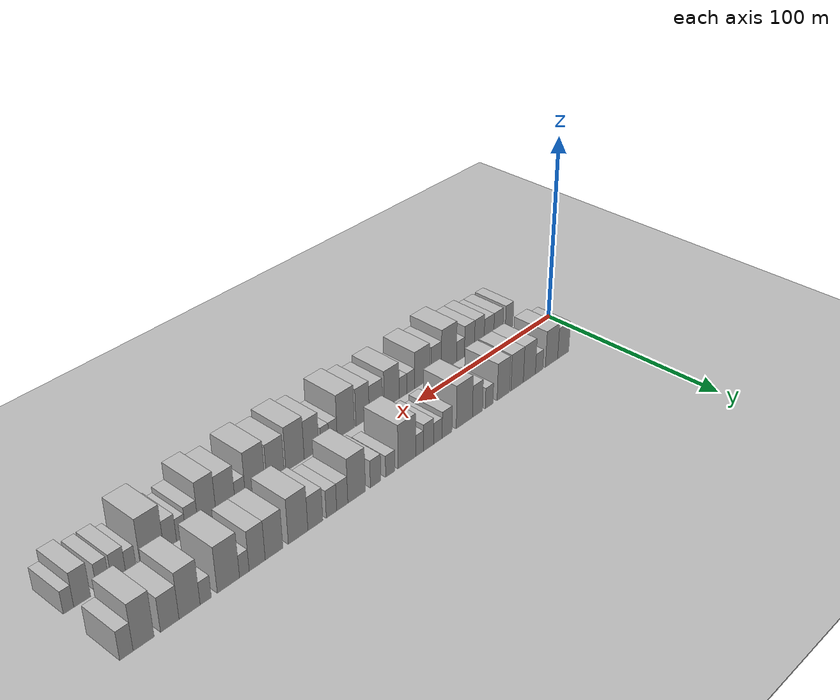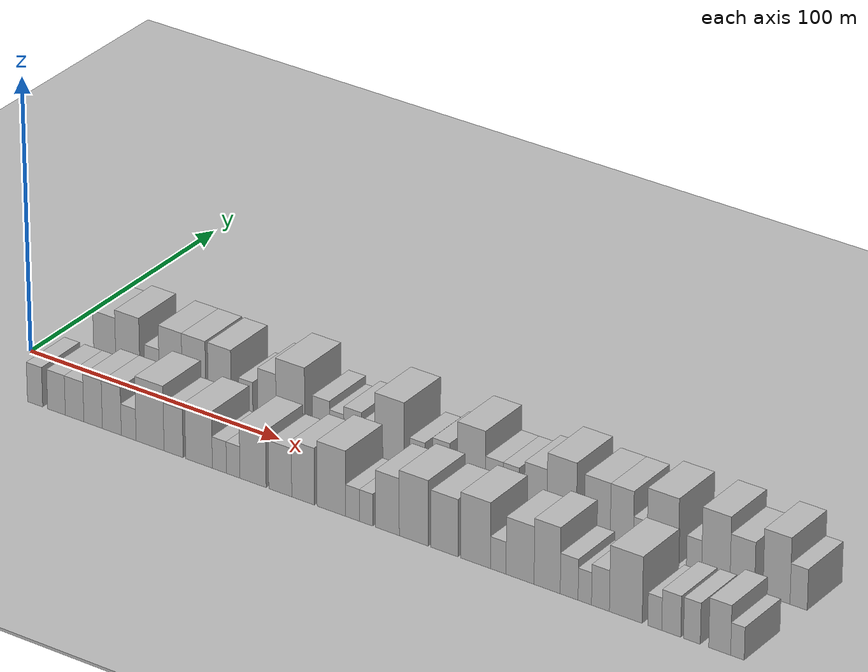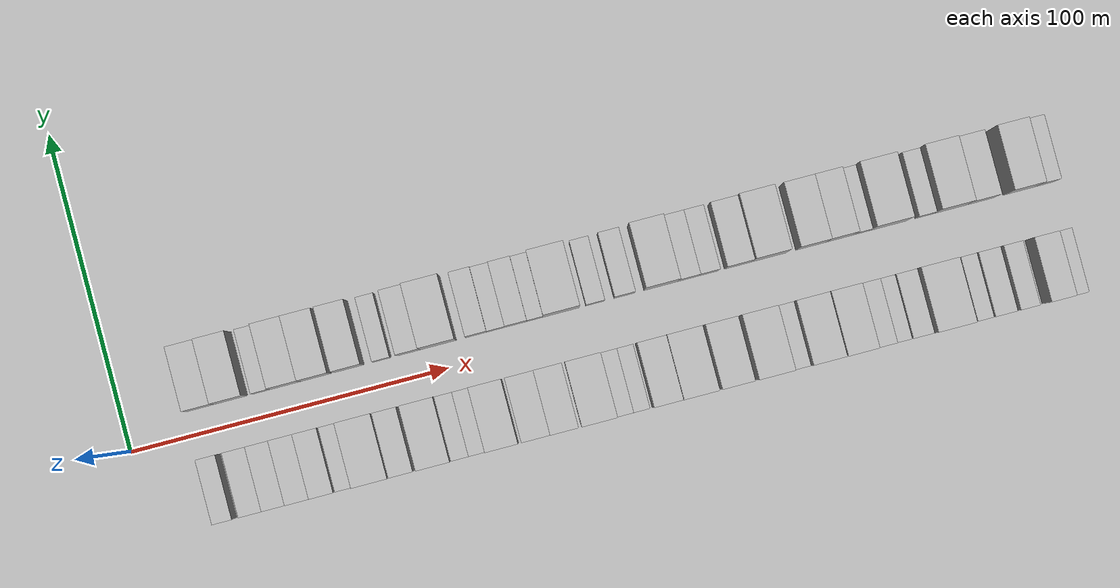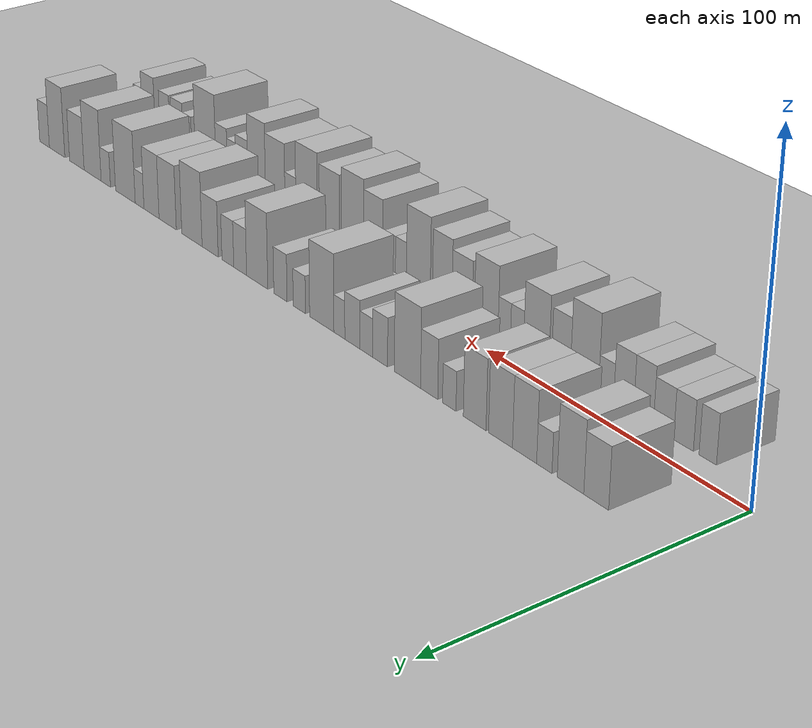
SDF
<?xml version="1.0" encoding="utf-8"?>

<sdf version="1.6">

   <world name="default">

      <gui fullscreen="0">

         <camera name="user_camera">

            <pose>-15 0 4.57585 0 0 0</pose>

            <view_controller>orbit</view_controller>

         </camera>

      </gui>

      <scene>

         <sky>

           <clouds>

             <speed>12</speed>

           </clouds>

         </sky>

         <ambient>0.4 0.4 0.4 1</ambient>

         <background>0.7 0.7 0.7 1</background>

         <shadows>1</shadows>

      </scene>

      <gravity>0 0 -9.8066</gravity>

      <magnetic_field>6e-06 2.3e-05 -4.2e-05</magnetic_field>

      <physics default="0" name="default_physics" type="ode">

         <ode>

            <solver>

               <type>quick</type>

               <iters>10</iters>

               <sor>1.0</sor>

               <use_dynamic_moi_rescaling>0</use_dynamic_moi_rescaling>

            </solver>

            <constraints>

               <cfm>0</cfm>

               <erp>0.2</erp>

               <contact_max_correcting_vel>100</contact_max_correcting_vel>

               <contact_surface_layer>0.001</contact_surface_layer>

            </constraints>

         </ode>

         <max_step_size>0.004</max_step_size>

         <real_time_factor>1</real_time_factor>

         <real_time_update_rate>250</real_time_update_rate>

      </physics>

      <light name="sun" type="directional">

         <cast_shadows>1</cast_shadows>

         <pose>0 0 10 0 0 0</pose>

         <diffuse>0.8 0.8 0.8 1</diffuse>

         <specular>0.2 0.2 0.2 1</specular>

         <attenuation>

            <range>1000</range>

            <constant>0.9</constant>

            <linear>0.01</linear>

            <quadratic>0.001</quadratic>

         </attenuation>

         <direction>-0.5 0.1 -0.9</direction>

      </light>

      <include>

         <name>ground_plane_1</name>

         <uri>model://HANNAS_ground_plane</uri>

         <pose>0 0 0  0 0 0</pose>

      </include>

      <include>

         <name>ground_plane_2</name>

         <uri>model://HANNAS_ground_plane</uri>

         <pose>100 0 0  0 0 0</pose>

      </include>

      <model name="building_1">

         <static>1</static>

         <pose frame="">24.4732 17.5000 0 0.000000 0.000000 1.570796</pose>

         <link name="link">

            <pose frame="">0 0 9.00 0 0 0</pose>

            <collision name="collision">

               <geometry>

                  <box>

                     <size>20.0000 8.9463 18.0000</size>

                  </box>

               </geometry>

               <max_contacts>10</max_contacts>

               <surface>

                  <contact>

                     <ode/>

                  </contact>

                  <bounce/>

                  <friction>

                     <torsional>

                        <ode/>

                     </torsional>

                     <ode/>

                  </friction>

               </surface>

            </collision>

            <visual name="visual">

               <cast_shadows>0</cast_shadows>

               <geometry>

                  <box>

                     <size>20.0000 8.9463 18.0000</size>

                  </box>

               </geometry>

               <material>

                  <script>

                     <uri>model://HANNAS_wall/materials/scripts</uri>

                     <uri>model://HANNAS_wall/materials/textures</uri>

                     <name>vrc/HANNAS_wall</name>

                  </script>

               </material>

            </visual>

            <self_collide>0</self_collide>

            <enable_wind>0</enable_wind>

            <kinematic>0</kinematic>

         </link>

      </model>

      <model name="building_2">

         <static>1</static>

         <pose frame="">33.8260 17.5000 0 0.000000 0.000000 1.570796</pose>

         <link name="link">

            <pose frame="">0 0 10.50 0 0 0</pose>

            <collision name="collision">

               <geometry>

                  <box>

                     <size>20.0000 9.7593 21.0000</size>

                  </box>

               </geometry>

               <max_contacts>10</max_contacts>

               <surface>

                  <contact>

                     <ode/>

                  </contact>

                  <bounce/>

                  <friction>

                     <torsional>

                        <ode/>

                     </torsional>

                     <ode/>

                  </friction>

               </surface>

            </collision>

            <visual name="visual">

               <cast_shadows>0</cast_shadows>

               <geometry>

                  <box>

                     <size>20.0000 9.7593 21.0000</size>

                  </box>

               </geometry>

               <material>

                  <script>

                     <uri>model://HANNAS_wall/materials/scripts</uri>

                     <uri>model://HANNAS_wall/materials/textures</uri>

                     <name>vrc/HANNAS_wall</name>

                  </script>

               </material>

            </visual>

            <self_collide>0</self_collide>

            <enable_wind>0</enable_wind>

            <kinematic>0</kinematic>

         </link>

      </model>

      <model name="building_3">

         <static>1</static>

         <pose frame="">43.6046 17.5000 0 0.000000 0.000000 1.570796</pose>

         <link name="link">

            <pose frame="">0 0 6.00 0 0 0</pose>

            <collision name="collision">

               <geometry>

                  <box>

                     <size>20.0000 5.7978 12.0000</size>

                  </box>

               </geometry>

               <max_contacts>10</max_contacts>

               <surface>

                  <contact>

                     <ode/>

                  </contact>

                  <bounce/>

                  <friction>

                     <torsional>

                        <ode/>

                     </torsional>

                     <ode/>

                  </friction>

               </surface>

            </collision>

            <visual name="visual">

               <cast_shadows>0</cast_shadows>

               <geometry>

                  <box>

                     <size>20.0000 5.7978 12.0000</size>

                  </box>

               </geometry>

               <material>

                  <script>

                     <uri>model://HANNAS_wall/materials/scripts</uri>

                     <uri>model://HANNAS_wall/materials/textures</uri>

                     <name>vrc/HANNAS_wall</name>

                  </script>

               </material>

            </visual>

            <self_collide>0</self_collide>

            <enable_wind>0</enable_wind>

            <kinematic>0</kinematic>

         </link>

      </model>

      <model name="building_4">

         <static>1</static>

         <pose frame="">51.1458 17.5000 0 0.000000 0.000000 1.570796</pose>

         <link name="link">

            <pose frame="">0 0 10.50 0 0 0</pose>

            <collision name="collision">

               <geometry>

                  <box>

                     <size>20.0000 9.2847 21.0000</size>

                  </box>

               </geometry>

               <max_contacts>10</max_contacts>

               <surface>

                  <contact>

                     <ode/>

                  </contact>

                  <bounce/>

                  <friction>

                     <torsional>

                        <ode/>

                     </torsional>

                     <ode/>

                  </friction>

               </surface>

            </collision>

            <visual name="visual">

               <cast_shadows>0</cast_shadows>

               <geometry>

                  <box>

                     <size>20.0000 9.2847 21.0000</size>

                  </box>

               </geometry>

               <material>

                  <script>

                     <uri>model://HANNAS_wall/materials/scripts</uri>

                     <uri>model://HANNAS_wall/materials/textures</uri>

                     <name>vrc/HANNAS_wall</name>

                  </script>

               </material>

            </visual>

            <self_collide>0</self_collide>

            <enable_wind>0</enable_wind>

            <kinematic>0</kinematic>

         </link>

      </model>

      <model name="building_5">

         <static>1</static>

         <pose frame="">60.5061 17.5000 0 0.000000 0.000000 1.570796</pose>

         <link name="link">

            <pose frame="">0 0 10.50 0 0 0</pose>

            <collision name="collision">

               <geometry>

                  <box>

                     <size>20.0000 9.4358 21.0000</size>

                  </box>

               </geometry>

               <max_contacts>10</max_contacts>

               <surface>

                  <contact>

                     <ode/>

                  </contact>

                  <bounce/>

                  <friction>

                     <torsional>

                        <ode/>

                     </torsional>

                     <ode/>

                  </friction>

               </surface>

            </collision>

            <visual name="visual">

               <cast_shadows>0</cast_shadows>

               <geometry>

                  <box>

                     <size>20.0000 9.4358 21.0000</size>

                  </box>

               </geometry>

               <material>

                  <script>

                     <uri>model://HANNAS_wall/materials/scripts</uri>

                     <uri>model://HANNAS_wall/materials/textures</uri>

                     <name>vrc/HANNAS_wall</name>

                  </script>

               </material>

            </visual>

            <self_collide>0</self_collide>

            <enable_wind>0</enable_wind>

            <kinematic>0</kinematic>

         </link>

      </model>

      <model name="building_6">

         <static>1</static>

         <pose frame="">70.8064 17.5000 0 0.000000 0.000000 1.570796</pose>

         <link name="link">

            <pose frame="">0 0 10.50 0 0 0</pose>

            <collision name="collision">

               <geometry>

                  <box>

                     <size>20.0000 9.1649 21.0000</size>

                  </box>

               </geometry>

               <max_contacts>10</max_contacts>

               <surface>

                  <contact>

                     <ode/>

                  </contact>

                  <bounce/>

                  <friction>

                     <torsional>

                        <ode/>

                     </torsional>

                     <ode/>

                  </friction>

               </surface>

            </collision>

            <visual name="visual">

               <cast_shadows>0</cast_shadows>

               <geometry>

                  <box>

                     <size>20.0000 9.1649 21.0000</size>

                  </box>

               </geometry>

               <material>

                  <script>

                     <uri>model://HANNAS_wall/materials/scripts</uri>

                     <uri>model://HANNAS_wall/materials/textures</uri>

                     <name>vrc/HANNAS_wall</name>

                  </script>

               </material>

            </visual>

            <self_collide>0</self_collide>

            <enable_wind>0</enable_wind>

            <kinematic>0</kinematic>

         </link>

      </model>

      <model name="building_7">

         <static>1</static>

         <pose frame="">81.1681 17.5000 0 0.000000 0.000000 1.570796</pose>

         <link name="link">

            <pose frame="">0 0 6.00 0 0 0</pose>

            <collision name="collision">

               <geometry>

                  <box>

                     <size>20.0000 5.5586 12.0000</size>

                  </box>

               </geometry>

               <max_contacts>10</max_contacts>

               <surface>

                  <contact>

                     <ode/>

                  </contact>

                  <bounce/>

                  <friction>

                     <torsional>

                        <ode/>

                     </torsional>

                     <ode/>

                  </friction>

               </surface>

            </collision>

            <visual name="visual">

               <cast_shadows>0</cast_shadows>

               <geometry>

                  <box>

                     <size>20.0000 5.5586 12.0000</size>

                  </box>

               </geometry>

               <material>

                  <script>

                     <uri>model://HANNAS_wall/materials/scripts</uri>

                     <uri>model://HANNAS_wall/materials/textures</uri>

                     <name>vrc/HANNAS_wall</name>

                  </script>

               </material>

            </visual>

            <self_collide>0</self_collide>

            <enable_wind>0</enable_wind>

            <kinematic>0</kinematic>

         </link>

      </model>

      <model name="building_8">

         <static>1</static>

         <pose frame="">89.5558 17.5000 0 0.000000 0.000000 1.570796</pose>

         <link name="link">

            <pose frame="">0 0 9.00 0 0 0</pose>

            <collision name="collision">

               <geometry>

                  <box>

                     <size>20.0000 7.2167 18.0000</size>

                  </box>

               </geometry>

               <max_contacts>10</max_contacts>

               <surface>

                  <contact>

                     <ode/>

                  </contact>

                  <bounce/>

                  <friction>

                     <torsional>

                        <ode/>

                     </torsional>

                     <ode/>

                  </friction>

               </surface>

            </collision>

            <visual name="visual">

               <cast_shadows>0</cast_shadows>

               <geometry>

                  <box>

                     <size>20.0000 7.2167 18.0000</size>

                  </box>

               </geometry>

               <material>

                  <script>

                     <uri>model://HANNAS_wall/materials/scripts</uri>

                     <uri>model://HANNAS_wall/materials/textures</uri>

                     <name>vrc/HANNAS_wall</name>

                  </script>

               </material>

            </visual>

            <self_collide>0</self_collide>

            <enable_wind>0</enable_wind>

            <kinematic>0</kinematic>

         </link>

      </model>

      <model name="building_9">

         <static>1</static>

         <pose frame="">98.8152 17.5000 0 0.000000 0.000000 1.570796</pose>

         <link name="link">

            <pose frame="">0 0 12.00 0 0 0</pose>

            <collision name="collision">

               <geometry>

                  <box>

                     <size>20.0000 11.3021 24.0000</size>

                  </box>

               </geometry>

               <max_contacts>10</max_contacts>

               <surface>

                  <contact>

                     <ode/>

                  </contact>

                  <bounce/>

                  <friction>

                     <torsional>

                        <ode/>

                     </torsional>

                     <ode/>

                  </friction>

               </surface>

            </collision>

            <visual name="visual">

               <cast_shadows>0</cast_shadows>

               <geometry>

                  <box>

                     <size>20.0000 11.3021 24.0000</size>

                  </box>

               </geometry>

               <material>

                  <script>

                     <uri>model://HANNAS_wall/materials/scripts</uri>

                     <uri>model://HANNAS_wall/materials/textures</uri>

                     <name>vrc/HANNAS_wall</name>

                  </script>

               </material>

            </visual>

            <self_collide>0</self_collide>

            <enable_wind>0</enable_wind>

            <kinematic>0</kinematic>

         </link>

      </model>

      <model name="building_10">

         <static>1</static>

         <pose frame="">110.7903 17.5000 0 0.000000 0.000000 1.570796</pose>

         <link name="link">

            <pose frame="">0 0 7.50 0 0 0</pose>

            <collision name="collision">

               <geometry>

                  <box>

                     <size>20.0000 6.6480 15.0000</size>

                  </box>

               </geometry>

               <max_contacts>10</max_contacts>

               <surface>

                  <contact>

                     <ode/>

                  </contact>

                  <bounce/>

                  <friction>

                     <torsional>

                        <ode/>

                     </torsional>

                     <ode/>

                  </friction>

               </surface>

            </collision>

            <visual name="visual">

               <cast_shadows>0</cast_shadows>

               <geometry>

                  <box>

                     <size>20.0000 6.6480 15.0000</size>

                  </box>

               </geometry>

               <material>

                  <script>

                     <uri>model://HANNAS_wall/materials/scripts</uri>

                     <uri>model://HANNAS_wall/materials/textures</uri>

                     <name>vrc/HANNAS_wall</name>

                  </script>

               </material>

            </visual>

            <self_collide>0</self_collide>

            <enable_wind>0</enable_wind>

            <kinematic>0</kinematic>

         </link>

      </model>

      <model name="building_11">

         <static>1</static>

         <pose frame="">116.9366 17.5000 0 0.000000 0.000000 1.570796</pose>

         <link name="link">

            <pose frame="">0 0 6.00 0 0 0</pose>

            <collision name="collision">

               <geometry>

                  <box>

                     <size>20.0000 5.6447 12.0000</size>

                  </box>

               </geometry>

               <max_contacts>10</max_contacts>

               <surface>

                  <contact>

                     <ode/>

                  </contact>

                  <bounce/>

                  <friction>

                     <torsional>

                        <ode/>

                     </torsional>

                     <ode/>

                  </friction>

               </surface>

            </collision>

            <visual name="visual">

               <cast_shadows>0</cast_shadows>

               <geometry>

                  <box>

                     <size>20.0000 5.6447 12.0000</size>

                  </box>

               </geometry>

               <material>

                  <script>

                     <uri>model://HANNAS_wall/materials/scripts</uri>

                     <uri>model://HANNAS_wall/materials/textures</uri>

                     <name>vrc/HANNAS_wall</name>

                  </script>

               </material>

            </visual>

            <self_collide>0</self_collide>

            <enable_wind>0</enable_wind>

            <kinematic>0</kinematic>

         </link>

      </model>

      <model name="building_12">

         <static>1</static>

         <pose frame="">123.2144 17.5000 0 0.000000 0.000000 1.570796</pose>

         <link name="link">

            <pose frame="">0 0 7.50 0 0 0</pose>

            <collision name="collision">

               <geometry>

                  <box>

                     <size>20.0000 6.9108 15.0000</size>

                  </box>

               </geometry>

               <max_contacts>10</max_contacts>

               <surface>

                  <contact>

                     <ode/>

                  </contact>

                  <bounce/>

                  <friction>

                     <torsional>

                        <ode/>

                     </torsional>

                     <ode/>

                  </friction>

               </surface>

            </collision>

            <visual name="visual">

               <cast_shadows>0</cast_shadows>

               <geometry>

                  <box>

                     <size>20.0000 6.9108 15.0000</size>

                  </box>

               </geometry>

               <material>

                  <script>

                     <uri>model://HANNAS_wall/materials/scripts</uri>

                     <uri>model://HANNAS_wall/materials/textures</uri>

                     <name>vrc/HANNAS_wall</name>

                  </script>

               </material>

            </visual>

            <self_collide>0</self_collide>

            <enable_wind>0</enable_wind>

            <kinematic>0</kinematic>

         </link>

      </model>

      <model name="building_13">

         <static>1</static>

         <pose frame="">129.1945 17.5000 0 0.000000 0.000000 1.570796</pose>

         <link name="link">

            <pose frame="">0 0 6.00 0 0 0</pose>

            <collision name="collision">

               <geometry>

                  <box>

                     <size>20.0000 5.0494 12.0000</size>

                  </box>

               </geometry>

               <max_contacts>10</max_contacts>

               <surface>

                  <contact>

                     <ode/>

                  </contact>

                  <bounce/>

                  <friction>

                     <torsional>

                        <ode/>

                     </torsional>

                     <ode/>

                  </friction>

               </surface>

            </collision>

            <visual name="visual">

               <cast_shadows>0</cast_shadows>

               <geometry>

                  <box>

                     <size>20.0000 5.0494 12.0000</size>

                  </box>

               </geometry>

               <material>

                  <script>

                     <uri>model://HANNAS_wall/materials/scripts</uri>

                     <uri>model://HANNAS_wall/materials/textures</uri>

                     <name>vrc/HANNAS_wall</name>

                  </script>

               </material>

            </visual>

            <self_collide>0</self_collide>

            <enable_wind>0</enable_wind>

            <kinematic>0</kinematic>

         </link>

      </model>

      <model name="building_14">

         <static>1</static>

         <pose frame="">137.4230 17.5000 0 0.000000 0.000000 1.570796</pose>

         <link name="link">

            <pose frame="">0 0 12.00 0 0 0</pose>

            <collision name="collision">

               <geometry>

                  <box>

                     <size>20.0000 11.4074 24.0000</size>

                  </box>

               </geometry>

               <max_contacts>10</max_contacts>

               <surface>

                  <contact>

                     <ode/>

                  </contact>

                  <bounce/>

                  <friction>

                     <torsional>

                        <ode/>

                     </torsional>

                     <ode/>

                  </friction>

               </surface>

            </collision>

            <visual name="visual">

               <cast_shadows>0</cast_shadows>

               <geometry>

                  <box>

                     <size>20.0000 11.4074 24.0000</size>

                  </box>

               </geometry>

               <material>

                  <script>

                     <uri>model://HANNAS_wall/materials/scripts</uri>

                     <uri>model://HANNAS_wall/materials/textures</uri>

                     <name>vrc/HANNAS_wall</name>

                  </script>

               </material>

            </visual>

            <self_collide>0</self_collide>

            <enable_wind>0</enable_wind>

            <kinematic>0</kinematic>

         </link>

      </model>

      <model name="building_15">

         <static>1</static>

         <pose frame="">148.0686 17.5000 0 0.000000 0.000000 1.570796</pose>

         <link name="link">

            <pose frame="">0 0 6.00 0 0 0</pose>

            <collision name="collision">

               <geometry>

                  <box>

                     <size>20.0000 5.8838 12.0000</size>

                  </box>

               </geometry>

               <max_contacts>10</max_contacts>

               <surface>

                  <contact>

                     <ode/>

                  </contact>

                  <bounce/>

                  <friction>

                     <torsional>

                        <ode/>

                     </torsional>

                     <ode/>

                  </friction>

               </surface>

            </collision>

            <visual name="visual">

               <cast_shadows>0</cast_shadows>

               <geometry>

                  <box>

                     <size>20.0000 5.8838 12.0000</size>

                  </box>

               </geometry>

               <material>

                  <script>

                     <uri>model://HANNAS_wall/materials/scripts</uri>

                     <uri>model://HANNAS_wall/materials/textures</uri>

                     <name>vrc/HANNAS_wall</name>

                  </script>

               </material>

            </visual>

            <self_collide>0</self_collide>

            <enable_wind>0</enable_wind>

            <kinematic>0</kinematic>

         </link>

      </model>

      <model name="building_16">

         <static>1</static>

         <pose frame="">157.2566 17.5000 0 0.000000 0.000000 1.570796</pose>

         <link name="link">

            <pose frame="">0 0 7.50 0 0 0</pose>

            <collision name="collision">

               <geometry>

                  <box>

                     <size>20.0000 6.4921 15.0000</size>

                  </box>

               </geometry>

               <max_contacts>10</max_contacts>

               <surface>

                  <contact>

                     <ode/>

                  </contact>

                  <bounce/>

                  <friction>

                     <torsional>

                        <ode/>

                     </torsional>

                     <ode/>

                  </friction>

               </surface>

            </collision>

            <visual name="visual">

               <cast_shadows>0</cast_shadows>

               <geometry>

                  <box>

                     <size>20.0000 6.4921 15.0000</size>

                  </box>

               </geometry>

               <material>

                  <script>

                     <uri>model://HANNAS_wall/materials/scripts</uri>

                     <uri>model://HANNAS_wall/materials/textures</uri>

                     <name>vrc/HANNAS_wall</name>

                  </script>

               </material>

            </visual>

            <self_collide>0</self_collide>

            <enable_wind>0</enable_wind>

            <kinematic>0</kinematic>

         </link>

      </model>

      <model name="building_17">

         <static>1</static>

         <pose frame="">168.8353 17.5000 0 0.000000 0.000000 1.570796</pose>

         <link name="link">

            <pose frame="">0 0 12.00 0 0 0</pose>

            <collision name="collision">

               <geometry>

                  <box>

                     <size>20.0000 10.6654 24.0000</size>

                  </box>

               </geometry>

               <max_contacts>10</max_contacts>

               <surface>

                  <contact>

                     <ode/>

                  </contact>

                  <bounce/>

                  <friction>

                     <torsional>

                        <ode/>

                     </torsional>

                     <ode/>

                  </friction>

               </surface>

            </collision>

            <visual name="visual">

               <cast_shadows>0</cast_shadows>

               <geometry>

                  <box>

                     <size>20.0000 10.6654 24.0000</size>

                  </box>

               </geometry>

               <material>

                  <script>

                     <uri>model://HANNAS_wall/materials/scripts</uri>

                     <uri>model://HANNAS_wall/materials/textures</uri>

                     <name>vrc/HANNAS_wall</name>

                  </script>

               </material>

            </visual>

            <self_collide>0</self_collide>

            <enable_wind>0</enable_wind>

            <kinematic>0</kinematic>

         </link>

      </model>

      <model name="building_18">

         <static>1</static>

         <pose frame="">177.4639 17.5000 0 0.000000 0.000000 1.570796</pose>

         <link name="link">

            <pose frame="">0 0 7.50 0 0 0</pose>

            <collision name="collision">

               <geometry>

                  <box>

                     <size>20.0000 6.5917 15.0000</size>

                  </box>

               </geometry>

               <max_contacts>10</max_contacts>

               <surface>

                  <contact>

                     <ode/>

                  </contact>

                  <bounce/>

                  <friction>

                     <torsional>

                        <ode/>

                     </torsional>

                     <ode/>

                  </friction>

               </surface>

            </collision>

            <visual name="visual">

               <cast_shadows>0</cast_shadows>

               <geometry>

                  <box>

                     <size>20.0000 6.5917 15.0000</size>

                  </box>

               </geometry>

               <material>

                  <script>

                     <uri>model://HANNAS_wall/materials/scripts</uri>

                     <uri>model://HANNAS_wall/materials/textures</uri>

                     <name>vrc/HANNAS_wall</name>

                  </script>

               </material>

            </visual>

            <self_collide>0</self_collide>

            <enable_wind>0</enable_wind>

            <kinematic>0</kinematic>

         </link>

      </model>

      <model name="building_19">

         <static>1</static>

         <pose frame="">183.8232 17.5000 0 0.000000 0.000000 1.570796</pose>

         <link name="link">

            <pose frame="">0 0 7.50 0 0 0</pose>

            <collision name="collision">

               <geometry>

                  <box>

                     <size>20.0000 6.1270 15.0000</size>

                  </box>

               </geometry>

               <max_contacts>10</max_contacts>

               <surface>

                  <contact>

                     <ode/>

                  </contact>

                  <bounce/>

                  <friction>

                     <torsional>

                        <ode/>

                     </torsional>

                     <ode/>

                  </friction>

               </surface>

            </collision>

            <visual name="visual">

               <cast_shadows>0</cast_shadows>

               <geometry>

                  <box>

                     <size>20.0000 6.1270 15.0000</size>

                  </box>

               </geometry>

               <material>

                  <script>

                     <uri>model://HANNAS_wall/materials/scripts</uri>

                     <uri>model://HANNAS_wall/materials/textures</uri>

                     <name>vrc/HANNAS_wall</name>

                  </script>

               </material>

            </visual>

            <self_collide>0</self_collide>

            <enable_wind>0</enable_wind>

            <kinematic>0</kinematic>

         </link>

      </model>

      <model name="building_20">

         <static>1</static>

         <pose frame="">193.1469 17.5000 0 0.000000 0.000000 1.570796</pose>

         <link name="link">

            <pose frame="">0 0 9.00 0 0 0</pose>

            <collision name="collision">

               <geometry>

                  <box>

                     <size>20.0000 8.5202 18.0000</size>

                  </box>

               </geometry>

               <max_contacts>10</max_contacts>

               <surface>

                  <contact>

                     <ode/>

                  </contact>

                  <bounce/>

                  <friction>

                     <torsional>

                        <ode/>

                     </torsional>

                     <ode/>

                  </friction>

               </surface>

            </collision>

            <visual name="visual">

               <cast_shadows>0</cast_shadows>

               <geometry>

                  <box>

                     <size>20.0000 8.5202 18.0000</size>

                  </box>

               </geometry>

               <material>

                  <script>

                     <uri>model://HANNAS_wall/materials/scripts</uri>

                     <uri>model://HANNAS_wall/materials/textures</uri>

                     <name>vrc/HANNAS_wall</name>

                  </script>

               </material>

            </visual>

            <self_collide>0</self_collide>

            <enable_wind>0</enable_wind>

            <kinematic>0</kinematic>

         </link>

      </model>

      <model name="building_21">

         <static>1</static>

         <pose frame="">202.9003 17.5000 0 0.000000 0.000000 1.570796</pose>

         <link name="link">

            <pose frame="">0 0 12.00 0 0 0</pose>

            <collision name="collision">

               <geometry>

                  <box>

                     <size>20.0000 10.9868 24.0000</size>

                  </box>

               </geometry>

               <max_contacts>10</max_contacts>

               <surface>

                  <contact>

                     <ode/>

                  </contact>

                  <bounce/>

                  <friction>

                     <torsional>

                        <ode/>

                     </torsional>

                     <ode/>

                  </friction>

               </surface>

            </collision>

            <visual name="visual">

               <cast_shadows>0</cast_shadows>

               <geometry>

                  <box>

                     <size>20.0000 10.9868 24.0000</size>

                  </box>

               </geometry>

               <material>

                  <script>

                     <uri>model://HANNAS_wall/materials/scripts</uri>

                     <uri>model://HANNAS_wall/materials/textures</uri>

                     <name>vrc/HANNAS_wall</name>

                  </script>

               </material>

            </visual>

            <self_collide>0</self_collide>

            <enable_wind>0</enable_wind>

            <kinematic>0</kinematic>

         </link>

      </model>

      <model name="building_22">

         <static>1</static>

         <pose frame="">216.1861 17.5000 0 0.000000 0.000000 1.570796</pose>

         <link name="link">

            <pose frame="">0 0 10.50 0 0 0</pose>

            <collision name="collision">

               <geometry>

                  <box>

                     <size>20.0000 9.5848 21.0000</size>

                  </box>

               </geometry>

               <max_contacts>10</max_contacts>

               <surface>

                  <contact>

                     <ode/>

                  </contact>

                  <bounce/>

                  <friction>

                     <torsional>

                        <ode/>

                     </torsional>

                     <ode/>

                  </friction>

               </surface>

            </collision>

            <visual name="visual">

               <cast_shadows>0</cast_shadows>

               <geometry>

                  <box>

                     <size>20.0000 9.5848 21.0000</size>

                  </box>

               </geometry>

               <material>

                  <script>

                     <uri>model://HANNAS_wall/materials/scripts</uri>

                     <uri>model://HANNAS_wall/materials/textures</uri>

                     <name>vrc/HANNAS_wall</name>

                  </script>

               </material>

            </visual>

            <self_collide>0</self_collide>

            <enable_wind>0</enable_wind>

            <kinematic>0</kinematic>

         </link>

      </model>

      <model name="building_23">

         <static>1</static>

         <pose frame="">225.2567 17.5000 0 0.000000 0.000000 1.570796</pose>

         <link name="link">

            <pose frame="">0 0 10.50 0 0 0</pose>

            <collision name="collision">

               <geometry>

                  <box>

                     <size>20.0000 8.5564 21.0000</size>

                  </box>

               </geometry>

               <max_contacts>10</max_contacts>

               <surface>

                  <contact>

                     <ode/>

                  </contact>

                  <bounce/>

                  <friction>

                     <torsional>

                        <ode/>

                     </torsional>

                     <ode/>

                  </friction>

               </surface>

            </collision>

            <visual name="visual">

               <cast_shadows>0</cast_shadows>

               <geometry>

                  <box>

                     <size>20.0000 8.5564 21.0000</size>

                  </box>

               </geometry>

               <material>

                  <script>

                     <uri>model://HANNAS_wall/materials/scripts</uri>

                     <uri>model://HANNAS_wall/materials/textures</uri>

                     <name>vrc/HANNAS_wall</name>

                  </script>

               </material>

            </visual>

            <self_collide>0</self_collide>

            <enable_wind>0</enable_wind>

            <kinematic>0</kinematic>

         </link>

      </model>

      <model name="building_24">

         <static>1</static>

         <pose frame="">232.0431 17.5000 0 0.000000 0.000000 1.570796</pose>

         <link name="link">

            <pose frame="">0 0 6.00 0 0 0</pose>

            <collision name="collision">

               <geometry>

                  <box>

                     <size>20.0000 5.0165 12.0000</size>

                  </box>

               </geometry>

               <max_contacts>10</max_contacts>

               <surface>

                  <contact>

                     <ode/>

                  </contact>

                  <bounce/>

                  <friction>

                     <torsional>

                        <ode/>

                     </torsional>

                     <ode/>

                  </friction>

               </surface>

            </collision>

            <visual name="visual">

               <cast_shadows>0</cast_shadows>

               <geometry>

                  <box>

                     <size>20.0000 5.0165 12.0000</size>

                  </box>

               </geometry>

               <material>

                  <script>

                     <uri>model://HANNAS_wall/materials/scripts</uri>

                     <uri>model://HANNAS_wall/materials/textures</uri>

                     <name>vrc/HANNAS_wall</name>

                  </script>

               </material>

            </visual>

            <self_collide>0</self_collide>

            <enable_wind>0</enable_wind>

            <kinematic>0</kinematic>

         </link>

      </model>

      <model name="building_25">

         <static>1</static>

         <pose frame="">240.2965 17.5000 0 0.000000 0.000000 1.570796</pose>

         <link name="link">

            <pose frame="">0 0 12.00 0 0 0</pose>

            <collision name="collision">

               <geometry>

                  <box>

                     <size>20.0000 11.4902 24.0000</size>

                  </box>

               </geometry>

               <max_contacts>10</max_contacts>

               <surface>

                  <contact>

                     <ode/>

                  </contact>

                  <bounce/>

                  <friction>

                     <torsional>

                        <ode/>

                     </torsional>

                     <ode/>

                  </friction>

               </surface>

            </collision>

            <visual name="visual">

               <cast_shadows>0</cast_shadows>

               <geometry>

                  <box>

                     <size>20.0000 11.4902 24.0000</size>

                  </box>

               </geometry>

               <material>

                  <script>

                     <uri>model://HANNAS_wall/materials/scripts</uri>

                     <uri>model://HANNAS_wall/materials/textures</uri>

                     <name>vrc/HANNAS_wall</name>

                  </script>

               </material>

            </visual>

            <self_collide>0</self_collide>

            <enable_wind>0</enable_wind>

            <kinematic>0</kinematic>

         </link>

      </model>

      <model name="building_26">

         <static>1</static>

         <pose frame="">251.8174 17.5000 0 0.000000 0.000000 1.570796</pose>

         <link name="link">

            <pose frame="">0 0 6.00 0 0 0</pose>

            <collision name="collision">

               <geometry>

                  <box>

                     <size>20.0000 5.5515 12.0000</size>

                  </box>

               </geometry>

               <max_contacts>10</max_contacts>

               <surface>

                  <contact>

                     <ode/>

                  </contact>

                  <bounce/>

                  <friction>

                     <torsional>

                        <ode/>

                     </torsional>

                     <ode/>

                  </friction>

               </surface>

            </collision>

            <visual name="visual">

               <cast_shadows>0</cast_shadows>

               <geometry>

                  <box>

                     <size>20.0000 5.5515 12.0000</size>

                  </box>

               </geometry>

               <material>

                  <script>

                     <uri>model://HANNAS_wall/materials/scripts</uri>

                     <uri>model://HANNAS_wall/materials/textures</uri>

                     <name>vrc/HANNAS_wall</name>

                  </script>

               </material>

            </visual>

            <self_collide>0</self_collide>

            <enable_wind>0</enable_wind>

            <kinematic>0</kinematic>

         </link>

      </model>

      <model name="building_27">

         <static>1</static>

         <pose frame="">259.7761 17.5000 0 0.000000 0.000000 1.570796</pose>

         <link name="link">

            <pose frame="">0 0 12.00 0 0 0</pose>

            <collision name="collision">

               <geometry>

                  <box>

                     <size>20.0000 10.3660 24.0000</size>

                  </box>

               </geometry>

               <max_contacts>10</max_contacts>

               <surface>

                  <contact>

                     <ode/>

                  </contact>

                  <bounce/>

                  <friction>

                     <torsional>

                        <ode/>

                     </torsional>

                     <ode/>

                  </friction>

               </surface>

            </collision>

            <visual name="visual">

               <cast_shadows>0</cast_shadows>

               <geometry>

                  <box>

                     <size>20.0000 10.3660 24.0000</size>

                  </box>

               </geometry>

               <material>

                  <script>

                     <uri>model://HANNAS_wall/materials/scripts</uri>

                     <uri>model://HANNAS_wall/materials/textures</uri>

                     <name>vrc/HANNAS_wall</name>

                  </script>

               </material>

            </visual>

            <self_collide>0</self_collide>

            <enable_wind>0</enable_wind>

            <kinematic>0</kinematic>

         </link>

      </model>

      <model name="building_28">

         <static>1</static>

         <pose frame="">269.4195 17.5000 0 0.000000 0.000000 1.570796</pose>

         <link name="link">

            <pose frame="">0 0 9.00 0 0 0</pose>

            <collision name="collision">

               <geometry>

                  <box>

                     <size>20.0000 8.9207 18.0000</size>

                  </box>

               </geometry>

               <max_contacts>10</max_contacts>

               <surface>

                  <contact>

                     <ode/>

                  </contact>

                  <bounce/>

                  <friction>

                     <torsional>

                        <ode/>

                     </torsional>

                     <ode/>

                  </friction>

               </surface>

            </collision>

            <visual name="visual">

               <cast_shadows>0</cast_shadows>

               <geometry>

                  <box>

                     <size>20.0000 8.9207 18.0000</size>

                  </box>

               </geometry>

               <material>

                  <script>

                     <uri>model://HANNAS_wall/materials/scripts</uri>

                     <uri>model://HANNAS_wall/materials/textures</uri>

                     <name>vrc/HANNAS_wall</name>

                  </script>

               </material>

            </visual>

            <self_collide>0</self_collide>

            <enable_wind>0</enable_wind>

            <kinematic>0</kinematic>

         </link>

      </model>

      <model name="building_29">

         <static>1</static>

         <pose frame="">281.7597 17.5000 0 0.000000 0.000000 1.570796</pose>

         <link name="link">

            <pose frame="">0 0 12.00 0 0 0</pose>

            <collision name="collision">

               <geometry>

                  <box>

                     <size>20.0000 9.7597 24.0000</size>

                  </box>

               </geometry>

               <max_contacts>10</max_contacts>

               <surface>

                  <contact>

                     <ode/>

                  </contact>

                  <bounce/>

                  <friction>

                     <torsional>

                        <ode/>

                     </torsional>

                     <ode/>

                  </friction>

               </surface>

            </collision>

            <visual name="visual">

               <cast_shadows>0</cast_shadows>

               <geometry>

                  <box>

                     <size>20.0000 9.7597 24.0000</size>

                  </box>

               </geometry>

               <material>

                  <script>

                     <uri>model://HANNAS_wall/materials/scripts</uri>

                     <uri>model://HANNAS_wall/materials/textures</uri>

                     <name>vrc/HANNAS_wall</name>

                  </script>

               </material>

            </visual>

            <self_collide>0</self_collide>

            <enable_wind>0</enable_wind>

            <kinematic>0</kinematic>

         </link>

      </model>

      <model name="building_30">

         <static>1</static>

         <pose frame="">289.7358 17.5000 0 0.000000 0.000000 1.570796</pose>

         <link name="link">

            <pose frame="">0 0 7.50 0 0 0</pose>

            <collision name="collision">

               <geometry>

                  <box>

                     <size>20.0000 6.1925 15.0000</size>

                  </box>

               </geometry>

               <max_contacts>10</max_contacts>

               <surface>

                  <contact>

                     <ode/>

                  </contact>

                  <bounce/>

                  <friction>

                     <torsional>

                        <ode/>

                     </torsional>

                     <ode/>

                  </friction>

               </surface>

            </collision>

            <visual name="visual">

               <cast_shadows>0</cast_shadows>

               <geometry>

                  <box>

                     <size>20.0000 6.1925 15.0000</size>

                  </box>

               </geometry>

               <material>

                  <script>

                     <uri>model://HANNAS_wall/materials/scripts</uri>

                     <uri>model://HANNAS_wall/materials/textures</uri>

                     <name>vrc/HANNAS_wall</name>

                  </script>

               </material>

            </visual>

            <self_collide>0</self_collide>

            <enable_wind>0</enable_wind>

            <kinematic>0</kinematic>

         </link>

      </model>

      <model name="building_31">

         <static>1</static>

         <pose frame="">23.0851 -17.5000 0 0.000000 0.000000 1.570796</pose>

         <link name="link">

            <pose frame="">0 0 7.50 0 0 0</pose>

            <collision name="collision">

               <geometry>

                  <box>

                     <size>20.0000 6.1702 15.0000</size>

                  </box>

               </geometry>

               <max_contacts>10</max_contacts>

               <surface>

                  <contact>

                     <ode/>

                  </contact>

                  <bounce/>

                  <friction>

                     <torsional>

                        <ode/>

                     </torsional>

                     <ode/>

                  </friction>

               </surface>

            </collision>

            <visual name="visual">

               <cast_shadows>0</cast_shadows>

               <geometry>

                  <box>

                     <size>20.0000 6.1702 15.0000</size>

                  </box>

               </geometry>

               <material>

                  <script>

                     <uri>model://HANNAS_wall/materials/scripts</uri>

                     <uri>model://HANNAS_wall/materials/textures</uri>

                     <name>vrc/HANNAS_wall</name>

                  </script>

               </material>

            </visual>

            <self_collide>0</self_collide>

            <enable_wind>0</enable_wind>

            <kinematic>0</kinematic>

         </link>

      </model>

      <model name="building_32">

         <static>1</static>

         <pose frame="">31.7403 -17.5000 0 0.000000 0.000000 1.570796</pose>

         <link name="link">

            <pose frame="">0 0 7.50 0 0 0</pose>

            <collision name="collision">

               <geometry>

                  <box>

                     <size>20.0000 7.1403 15.0000</size>

                  </box>

               </geometry>

               <max_contacts>10</max_contacts>

               <surface>

                  <contact>

                     <ode/>

                  </contact>

                  <bounce/>

                  <friction>

                     <torsional>

                        <ode/>

                     </torsional>

                     <ode/>

                  </friction>

               </surface>

            </collision>

            <visual name="visual">

               <cast_shadows>0</cast_shadows>

               <geometry>

                  <box>

                     <size>20.0000 7.1403 15.0000</size>

                  </box>

               </geometry>

               <material>

                  <script>

                     <uri>model://HANNAS_wall/materials/scripts</uri>

                     <uri>model://HANNAS_wall/materials/textures</uri>

                     <name>vrc/HANNAS_wall</name>

                  </script>

               </material>

            </visual>

            <self_collide>0</self_collide>

            <enable_wind>0</enable_wind>

            <kinematic>0</kinematic>

         </link>

      </model>

      <model name="building_33">

         <static>1</static>

         <pose frame="">39.0453 -17.5000 0 0.000000 0.000000 1.570796</pose>

         <link name="link">

            <pose frame="">0 0 7.50 0 0 0</pose>

            <collision name="collision">

               <geometry>

                  <box>

                     <size>20.0000 7.4695 15.0000</size>

                  </box>

               </geometry>

               <max_contacts>10</max_contacts>

               <surface>

                  <contact>

                     <ode/>

                  </contact>

                  <bounce/>

                  <friction>

                     <torsional>

                        <ode/>

                     </torsional>

                     <ode/>

                  </friction>

               </surface>

            </collision>

            <visual name="visual">

               <cast_shadows>0</cast_shadows>

               <geometry>

                  <box>

                     <size>20.0000 7.4695 15.0000</size>

                  </box>

               </geometry>

               <material>

                  <script>

                     <uri>model://HANNAS_wall/materials/scripts</uri>

                     <uri>model://HANNAS_wall/materials/textures</uri>

                     <name>vrc/HANNAS_wall</name>

                  </script>

               </material>

            </visual>

            <self_collide>0</self_collide>

            <enable_wind>0</enable_wind>

            <kinematic>0</kinematic>

         </link>

      </model>

      <model name="building_34">

         <static>1</static>

         <pose frame="">46.4872 -17.5000 0 0.000000 0.000000 1.570796</pose>

         <link name="link">

            <pose frame="">0 0 9.00 0 0 0</pose>

            <collision name="collision">

               <geometry>

                  <box>

                     <size>20.0000 7.4143 18.0000</size>

                  </box>

               </geometry>

               <max_contacts>10</max_contacts>

               <surface>

                  <contact>

                     <ode/>

                  </contact>

                  <bounce/>

                  <friction>

                     <torsional>

                        <ode/>

                     </torsional>

                     <ode/>

                  </friction>

               </surface>

            </collision>

            <visual name="visual">

               <cast_shadows>0</cast_shadows>

               <geometry>

                  <box>

                     <size>20.0000 7.4143 18.0000</size>

                  </box>

               </geometry>

               <material>

                  <script>

                     <uri>model://HANNAS_wall/materials/scripts</uri>

                     <uri>model://HANNAS_wall/materials/textures</uri>

                     <name>vrc/HANNAS_wall</name>

                  </script>

               </material>

            </visual>

            <self_collide>0</self_collide>

            <enable_wind>0</enable_wind>

            <kinematic>0</kinematic>

         </link>

      </model>

      <model name="building_35">

         <static>1</static>

         <pose frame="">53.9742 -17.5000 0 0.000000 0.000000 1.570796</pose>

         <link name="link">

            <pose frame="">0 0 9.00 0 0 0</pose>

            <collision name="collision">

               <geometry>

                  <box>

                     <size>20.0000 7.5598 18.0000</size>

                  </box>

               </geometry>

               <max_contacts>10</max_contacts>

               <surface>

                  <contact>

                     <ode/>

                  </contact>

                  <bounce/>

                  <friction>

                     <torsional>

                        <ode/>

                     </torsional>

                     <ode/>

                  </friction>

               </surface>

            </collision>

            <visual name="visual">

               <cast_shadows>0</cast_shadows>

               <geometry>

                  <box>

                     <size>20.0000 7.5598 18.0000</size>

                  </box>

               </geometry>

               <material>

                  <script>

                     <uri>model://HANNAS_wall/materials/scripts</uri>

                     <uri>model://HANNAS_wall/materials/textures</uri>

                     <name>vrc/HANNAS_wall</name>

                  </script>

               </material>

            </visual>

            <self_collide>0</self_collide>

            <enable_wind>0</enable_wind>

            <kinematic>0</kinematic>

         </link>

      </model>

      <model name="building_36">

         <static>1</static>

         <pose frame="">60.7030 -17.5000 0 0.000000 0.000000 1.570796</pose>

         <link name="link">

            <pose frame="">0 0 6.00 0 0 0</pose>

            <collision name="collision">

               <geometry>

                  <box>

                     <size>20.0000 5.8978 12.0000</size>

                  </box>

               </geometry>

               <max_contacts>10</max_contacts>

               <surface>

                  <contact>

                     <ode/>

                  </contact>

                  <bounce/>

                  <friction>

                     <torsional>

                        <ode/>

                     </torsional>

                     <ode/>

                  </friction>

               </surface>

            </collision>

            <visual name="visual">

               <cast_shadows>0</cast_shadows>

               <geometry>

                  <box>

                     <size>20.0000 5.8978 12.0000</size>

                  </box>

               </geometry>

               <material>

                  <script>

                     <uri>model://HANNAS_wall/materials/scripts</uri>

                     <uri>model://HANNAS_wall/materials/textures</uri>

                     <name>vrc/HANNAS_wall</name>

                  </script>

               </material>

            </visual>

            <self_collide>0</self_collide>

            <enable_wind>0</enable_wind>

            <kinematic>0</kinematic>

         </link>

      </model>

      <model name="building_37">

         <static>1</static>

         <pose frame="">69.2000 -17.5000 0 0.000000 0.000000 1.570796</pose>

         <link name="link">

            <pose frame="">0 0 12.00 0 0 0</pose>

            <collision name="collision">

               <geometry>

                  <box>

                     <size>20.0000 11.0962 24.0000</size>

                  </box>

               </geometry>

               <max_contacts>10</max_contacts>

               <surface>

                  <contact>

                     <ode/>

                  </contact>

                  <bounce/>

                  <friction>

                     <torsional>

                        <ode/>

                     </torsional>

                     <ode/>

                  </friction>

               </surface>

            </collision>

            <visual name="visual">

               <cast_shadows>0</cast_shadows>

               <geometry>

                  <box>

                     <size>20.0000 11.0962 24.0000</size>

                  </box>

               </geometry>

               <material>

                  <script>

                     <uri>model://HANNAS_wall/materials/scripts</uri>

                     <uri>model://HANNAS_wall/materials/textures</uri>

                     <name>vrc/HANNAS_wall</name>

                  </script>

               </material>

            </visual>

            <self_collide>0</self_collide>

            <enable_wind>0</enable_wind>

            <kinematic>0</kinematic>

         </link>

      </model>

      <model name="building_38">

         <static>1</static>

         <pose frame="">78.5195 -17.5000 0 0.000000 0.000000 1.570796</pose>

         <link name="link">

            <pose frame="">0 0 9.00 0 0 0</pose>

            <collision name="collision">

               <geometry>

                  <box>

                     <size>20.0000 7.5427 18.0000</size>

                  </box>

               </geometry>

               <max_contacts>10</max_contacts>

               <surface>

                  <contact>

                     <ode/>

                  </contact>

                  <bounce/>

                  <friction>

                     <torsional>

                        <ode/>

                     </torsional>

                     <ode/>

                  </friction>

               </surface>

            </collision>

            <visual name="visual">

               <cast_shadows>0</cast_shadows>

               <geometry>

                  <box>

                     <size>20.0000 7.5427 18.0000</size>

                  </box>

               </geometry>

               <material>

                  <script>

                     <uri>model://HANNAS_wall/materials/scripts</uri>

                     <uri>model://HANNAS_wall/materials/textures</uri>

                     <name>vrc/HANNAS_wall</name>

                  </script>

               </material>

            </visual>

            <self_collide>0</self_collide>

            <enable_wind>0</enable_wind>

            <kinematic>0</kinematic>

         </link>

      </model>

      <model name="building_39">

         <static>1</static>

         <pose frame="">88.5341 -17.5000 0 0.000000 0.000000 1.570796</pose>

         <link name="link">

            <pose frame="">0 0 10.50 0 0 0</pose>

            <collision name="collision">

               <geometry>

                  <box>

                     <size>20.0000 10.4865 21.0000</size>

                  </box>

               </geometry>

               <max_contacts>10</max_contacts>

               <surface>

                  <contact>

                     <ode/>

                  </contact>

                  <bounce/>

                  <friction>

                     <torsional>

                        <ode/>

                     </torsional>

                     <ode/>

                  </friction>

               </surface>

            </collision>

            <visual name="visual">

               <cast_shadows>0</cast_shadows>

               <geometry>

                  <box>

                     <size>20.0000 10.4865 21.0000</size>

                  </box>

               </geometry>

               <material>

                  <script>

                     <uri>model://HANNAS_wall/materials/scripts</uri>

                     <uri>model://HANNAS_wall/materials/textures</uri>

                     <name>vrc/HANNAS_wall</name>

                  </script>

               </material>

            </visual>

            <self_collide>0</self_collide>

            <enable_wind>0</enable_wind>

            <kinematic>0</kinematic>

         </link>

      </model>

      <model name="building_40">

         <static>1</static>

         <pose frame="">96.5365 -17.5000 0 0.000000 0.000000 1.570796</pose>

         <link name="link">

            <pose frame="">0 0 6.00 0 0 0</pose>

            <collision name="collision">

               <geometry>

                  <box>

                     <size>20.0000 5.5183 12.0000</size>

                  </box>

               </geometry>

               <max_contacts>10</max_contacts>

               <surface>

                  <contact>

                     <ode/>

                  </contact>

                  <bounce/>

                  <friction>

                     <torsional>

                        <ode/>

                     </torsional>

                     <ode/>

                  </friction>

               </surface>

            </collision>

            <visual name="visual">

               <cast_shadows>0</cast_shadows>

               <geometry>

                  <box>

                     <size>20.0000 5.5183 12.0000</size>

                  </box>

               </geometry>

               <material>

                  <script>

                     <uri>model://HANNAS_wall/materials/scripts</uri>

                     <uri>model://HANNAS_wall/materials/textures</uri>

                     <name>vrc/HANNAS_wall</name>

                  </script>

               </material>

            </visual>

            <self_collide>0</self_collide>

            <enable_wind>0</enable_wind>

            <kinematic>0</kinematic>

         </link>

      </model>

      <model name="building_41">

         <static>1</static>

         <pose frame="">101.9271 -17.5000 0 0.000000 0.000000 1.570796</pose>

         <link name="link">

            <pose frame="">0 0 6.00 0 0 0</pose>

            <collision name="collision">

               <geometry>

                  <box>

                     <size>20.0000 5.2628 12.0000</size>

                  </box>

               </geometry>

               <max_contacts>10</max_contacts>

               <surface>

                  <contact>

                     <ode/>

                  </contact>

                  <bounce/>

                  <friction>

                     <torsional>

                        <ode/>

                     </torsional>

                     <ode/>

                  </friction>

               </surface>

            </collision>

            <visual name="visual">

               <cast_shadows>0</cast_shadows>

               <geometry>

                  <box>

                     <size>20.0000 5.2628 12.0000</size>

                  </box>

               </geometry>

               <material>

                  <script>

                     <uri>model://HANNAS_wall/materials/scripts</uri>

                     <uri>model://HANNAS_wall/materials/textures</uri>

                     <name>vrc/HANNAS_wall</name>

                  </script>

               </material>

            </visual>

            <self_collide>0</self_collide>

            <enable_wind>0</enable_wind>

            <kinematic>0</kinematic>

         </link>

      </model>

      <model name="building_42">

         <static>1</static>

         <pose frame="">109.6693 -17.5000 0 0.000000 0.000000 1.570796</pose>

         <link name="link">

            <pose frame="">0 0 10.50 0 0 0</pose>

            <collision name="collision">

               <geometry>

                  <box>

                     <size>20.0000 10.2217 21.0000</size>

                  </box>

               </geometry>

               <max_contacts>10</max_contacts>

               <surface>

                  <contact>

                     <ode/>

                  </contact>

                  <bounce/>

                  <friction>

                     <torsional>

                        <ode/>

                     </torsional>

                     <ode/>

                  </friction>

               </surface>

            </collision>

            <visual name="visual">

               <cast_shadows>0</cast_shadows>

               <geometry>

                  <box>

                     <size>20.0000 10.2217 21.0000</size>

                  </box>

               </geometry>

               <material>

                  <script>

                     <uri>model://HANNAS_wall/materials/scripts</uri>

                     <uri>model://HANNAS_wall/materials/textures</uri>

                     <name>vrc/HANNAS_wall</name>

                  </script>

               </material>

            </visual>

            <self_collide>0</self_collide>

            <enable_wind>0</enable_wind>

            <kinematic>0</kinematic>

         </link>

      </model>

      <model name="building_43">

         <static>1</static>

         <pose frame="">120.2345 -17.5000 0 0.000000 0.000000 1.570796</pose>

         <link name="link">

            <pose frame="">0 0 9.00 0 0 0</pose>

            <collision name="collision">

               <geometry>

                  <box>

                     <size>20.0000 8.9088 18.0000</size>

                  </box>

               </geometry>

               <max_contacts>10</max_contacts>

               <surface>

                  <contact>

                     <ode/>

                  </contact>

                  <bounce/>

                  <friction>

                     <torsional>

                        <ode/>

                     </torsional>

                     <ode/>

                  </friction>

               </surface>

            </collision>

            <visual name="visual">

               <cast_shadows>0</cast_shadows>

               <geometry>

                  <box>

                     <size>20.0000 8.9088 18.0000</size>

                  </box>

               </geometry>

               <material>

                  <script>

                     <uri>model://HANNAS_wall/materials/scripts</uri>

                     <uri>model://HANNAS_wall/materials/textures</uri>

                     <name>vrc/HANNAS_wall</name>

                  </script>

               </material>

            </visual>

            <self_collide>0</self_collide>

            <enable_wind>0</enable_wind>

            <kinematic>0</kinematic>

         </link>

      </model>

      <model name="building_44">

         <static>1</static>

         <pose frame="">129.0713 -17.5000 0 0.000000 0.000000 1.570796</pose>

         <link name="link">

            <pose frame="">0 0 10.50 0 0 0</pose>

            <collision name="collision">

               <geometry>

                  <box>

                     <size>20.0000 8.7648 21.0000</size>

                  </box>

               </geometry>

               <max_contacts>10</max_contacts>

               <surface>

                  <contact>

                     <ode/>

                  </contact>

                  <bounce/>

                  <friction>

                     <torsional>

                        <ode/>

                     </torsional>

                     <ode/>

                  </friction>

               </surface>

            </collision>

            <visual name="visual">

               <cast_shadows>0</cast_shadows>

               <geometry>

                  <box>

                     <size>20.0000 8.7648 21.0000</size>

                  </box>

               </geometry>

               <material>

                  <script>

                     <uri>model://HANNAS_wall/materials/scripts</uri>

                     <uri>model://HANNAS_wall/materials/textures</uri>

                     <name>vrc/HANNAS_wall</name>

                  </script>

               </material>

            </visual>

            <self_collide>0</self_collide>

            <enable_wind>0</enable_wind>

            <kinematic>0</kinematic>

         </link>

      </model>

      <model name="building_45">

         <static>1</static>

         <pose frame="">139.9456 -17.5000 0 0.000000 0.000000 1.570796</pose>

         <link name="link">

            <pose frame="">0 0 12.00 0 0 0</pose>

            <collision name="collision">

               <geometry>

                  <box>

                     <size>20.0000 10.9838 24.0000</size>

                  </box>

               </geometry>

               <max_contacts>10</max_contacts>

               <surface>

                  <contact>

                     <ode/>

                  </contact>

                  <bounce/>

                  <friction>

                     <torsional>

                        <ode/>

                     </torsional>

                     <ode/>

                  </friction>

               </surface>

            </collision>

            <visual name="visual">

               <cast_shadows>0</cast_shadows>

               <geometry>

                  <box>

                     <size>20.0000 10.9838 24.0000</size>

                  </box>

               </geometry>

               <material>

                  <script>

                     <uri>model://HANNAS_wall/materials/scripts</uri>

                     <uri>model://HANNAS_wall/materials/textures</uri>

                     <name>vrc/HANNAS_wall</name>

                  </script>

               </material>

            </visual>

            <self_collide>0</self_collide>

            <enable_wind>0</enable_wind>

            <kinematic>0</kinematic>

         </link>

      </model>

      <model name="building_46">

         <static>1</static>

         <pose frame="">148.0660 -17.5000 0 0.000000 0.000000 1.570796</pose>

         <link name="link">

            <pose frame="">0 0 6.00 0 0 0</pose>

            <collision name="collision">

               <geometry>

                  <box>

                     <size>20.0000 5.2570 12.0000</size>

                  </box>

               </geometry>

               <max_contacts>10</max_contacts>

               <surface>

                  <contact>

                     <ode/>

                  </contact>

                  <bounce/>

                  <friction>

                     <torsional>

                        <ode/>

                     </torsional>

                     <ode/>

                  </friction>

               </surface>

            </collision>

            <visual name="visual">

               <cast_shadows>0</cast_shadows>

               <geometry>

                  <box>

                     <size>20.0000 5.2570 12.0000</size>

                  </box>

               </geometry>

               <material>

                  <script>

                     <uri>model://HANNAS_wall/materials/scripts</uri>

                     <uri>model://HANNAS_wall/materials/textures</uri>

                     <name>vrc/HANNAS_wall</name>

                  </script>

               </material>

            </visual>

            <self_collide>0</self_collide>

            <enable_wind>0</enable_wind>

            <kinematic>0</kinematic>

         </link>

      </model>

      <model name="building_47">

         <static>1</static>

         <pose frame="">153.2281 -17.5000 0 0.000000 0.000000 1.570796</pose>

         <link name="link">

            <pose frame="">0 0 6.00 0 0 0</pose>

            <collision name="collision">

               <geometry>

                  <box>

                     <size>20.0000 5.0671 12.0000</size>

                  </box>

               </geometry>

               <max_contacts>10</max_contacts>

               <surface>

                  <contact>

                     <ode/>

                  </contact>

                  <bounce/>

                  <friction>

                     <torsional>

                        <ode/>

                     </torsional>

                     <ode/>

                  </friction>

               </surface>

            </collision>

            <visual name="visual">

               <cast_shadows>0</cast_shadows>

               <geometry>

                  <box>

                     <size>20.0000 5.0671 12.0000</size>

                  </box>

               </geometry>

               <material>

                  <script>

                     <uri>model://HANNAS_wall/materials/scripts</uri>

                     <uri>model://HANNAS_wall/materials/textures</uri>

                     <name>vrc/HANNAS_wall</name>

                  </script>

               </material>

            </visual>

            <self_collide>0</self_collide>

            <enable_wind>0</enable_wind>

            <kinematic>0</kinematic>

         </link>

      </model>

      <model name="building_48">

         <static>1</static>

         <pose frame="">161.2894 -17.5000 0 0.000000 0.000000 1.570796</pose>

         <link name="link">

            <pose frame="">0 0 10.50 0 0 0</pose>

            <collision name="collision">

               <geometry>

                  <box>

                     <size>20.0000 9.0556 21.0000</size>

                  </box>

               </geometry>

               <max_contacts>10</max_contacts>

               <surface>

                  <contact>

                     <ode/>

                  </contact>

                  <bounce/>

                  <friction>

                     <torsional>

                        <ode/>

                     </torsional>

                     <ode/>

                  </friction>

               </surface>

            </collision>

            <visual name="visual">

               <cast_shadows>0</cast_shadows>

               <geometry>

                  <box>

                     <size>20.0000 9.0556 21.0000</size>

                  </box>

               </geometry>

               <material>

                  <script>

                     <uri>model://HANNAS_wall/materials/scripts</uri>

                     <uri>model://HANNAS_wall/materials/textures</uri>

                     <name>vrc/HANNAS_wall</name>

                  </script>

               </material>

            </visual>

            <self_collide>0</self_collide>

            <enable_wind>0</enable_wind>

            <kinematic>0</kinematic>

         </link>

      </model>

      <model name="building_49">

         <static>1</static>

         <pose frame="">171.3125 -17.5000 0 0.000000 0.000000 1.570796</pose>

         <link name="link">

            <pose frame="">0 0 12.00 0 0 0</pose>

            <collision name="collision">

               <geometry>

                  <box>

                     <size>20.0000 10.9906 24.0000</size>

                  </box>

               </geometry>

               <max_contacts>10</max_contacts>

               <surface>

                  <contact>

                     <ode/>

                  </contact>

                  <bounce/>

                  <friction>

                     <torsional>

                        <ode/>

                     </torsional>

                     <ode/>

                  </friction>

               </surface>

            </collision>

            <visual name="visual">

               <cast_shadows>0</cast_shadows>

               <geometry>

                  <box>

                     <size>20.0000 10.9906 24.0000</size>

                  </box>

               </geometry>

               <material>

                  <script>

                     <uri>model://HANNAS_wall/materials/scripts</uri>

                     <uri>model://HANNAS_wall/materials/textures</uri>

                     <name>vrc/HANNAS_wall</name>

                  </script>

               </material>

            </visual>

            <self_collide>0</self_collide>

            <enable_wind>0</enable_wind>

            <kinematic>0</kinematic>

         </link>

      </model>

      <model name="building_50">

         <static>1</static>

         <pose frame="">182.8734 -17.5000 0 0.000000 0.000000 1.570796</pose>

         <link name="link">

            <pose frame="">0 0 10.50 0 0 0</pose>

            <collision name="collision">

               <geometry>

                  <box>

                     <size>20.0000 10.1313 21.0000</size>

                  </box>

               </geometry>

               <max_contacts>10</max_contacts>

               <surface>

                  <contact>

                     <ode/>

                  </contact>

                  <bounce/>

                  <friction>

                     <torsional>

                        <ode/>

                     </torsional>

                     <ode/>

                  </friction>

               </surface>

            </collision>

            <visual name="visual">

               <cast_shadows>0</cast_shadows>

               <geometry>

                  <box>

                     <size>20.0000 10.1313 21.0000</size>

                  </box>

               </geometry>

               <material>

                  <script>

                     <uri>model://HANNAS_wall/materials/scripts</uri>

                     <uri>model://HANNAS_wall/materials/textures</uri>

                     <name>vrc/HANNAS_wall</name>

                  </script>

               </material>

            </visual>

            <self_collide>0</self_collide>

            <enable_wind>0</enable_wind>

            <kinematic>0</kinematic>

         </link>

      </model>

      <model name="building_51">

         <static>1</static>

         <pose frame="">194.5248 -17.5000 0 0.000000 0.000000 1.570796</pose>

         <link name="link">

            <pose frame="">0 0 12.00 0 0 0</pose>

            <collision name="collision">

               <geometry>

                  <box>

                     <size>20.0000 11.1714 24.0000</size>

                  </box>

               </geometry>

               <max_contacts>10</max_contacts>

               <surface>

                  <contact>

                     <ode/>

                  </contact>

                  <bounce/>

                  <friction>

                     <torsional>

                        <ode/>

                     </torsional>

                     <ode/>

                  </friction>

               </surface>

            </collision>

            <visual name="visual">

               <cast_shadows>0</cast_shadows>

               <geometry>

                  <box>

                     <size>20.0000 11.1714 24.0000</size>

                  </box>

               </geometry>

               <material>

                  <script>

                     <uri>model://HANNAS_wall/materials/scripts</uri>

                     <uri>model://HANNAS_wall/materials/textures</uri>

                     <name>vrc/HANNAS_wall</name>

                  </script>

               </material>

            </visual>

            <self_collide>0</self_collide>

            <enable_wind>0</enable_wind>

            <kinematic>0</kinematic>

         </link>

      </model>

      <model name="building_52">

         <static>1</static>

         <pose frame="">202.9877 -17.5000 0 0.000000 0.000000 1.570796</pose>

         <link name="link">

            <pose frame="">0 0 6.00 0 0 0</pose>

            <collision name="collision">

               <geometry>

                  <box>

                     <size>20.0000 5.7544 12.0000</size>

                  </box>

               </geometry>

               <max_contacts>10</max_contacts>

               <surface>

                  <contact>

                     <ode/>

                  </contact>

                  <bounce/>

                  <friction>

                     <torsional>

                        <ode/>

                     </torsional>

                     <ode/>

                  </friction>

               </surface>

            </collision>

            <visual name="visual">

               <cast_shadows>0</cast_shadows>

               <geometry>

                  <box>

                     <size>20.0000 5.7544 12.0000</size>

                  </box>

               </geometry>

               <material>

                  <script>

                     <uri>model://HANNAS_wall/materials/scripts</uri>

                     <uri>model://HANNAS_wall/materials/textures</uri>

                     <name>vrc/HANNAS_wall</name>

                  </script>

               </material>

            </visual>

            <self_collide>0</self_collide>

            <enable_wind>0</enable_wind>

            <kinematic>0</kinematic>

         </link>

      </model>

      <model name="building_53">

         <static>1</static>

         <pose frame="">211.0605 -17.5000 0 0.000000 0.000000 1.570796</pose>

         <link name="link">

            <pose frame="">0 0 10.50 0 0 0</pose>

            <collision name="collision">

               <geometry>

                  <box>

                     <size>20.0000 10.3911 21.0000</size>

                  </box>

               </geometry>

               <max_contacts>10</max_contacts>

               <surface>

                  <contact>

                     <ode/>

                  </contact>

                  <bounce/>

                  <friction>

                     <torsional>

                        <ode/>

                     </torsional>

                     <ode/>

                  </friction>

               </surface>

            </collision>

            <visual name="visual">

               <cast_shadows>0</cast_shadows>

               <geometry>

                  <box>

                     <size>20.0000 10.3911 21.0000</size>

                  </box>

               </geometry>

               <material>

                  <script>

                     <uri>model://HANNAS_wall/materials/scripts</uri>

                     <uri>model://HANNAS_wall/materials/textures</uri>

                     <name>vrc/HANNAS_wall</name>

                  </script>

               </material>

            </visual>

            <self_collide>0</self_collide>

            <enable_wind>0</enable_wind>

            <kinematic>0</kinematic>

         </link>

      </model>

      <model name="building_54">

         <static>1</static>

         <pose frame="">221.0789 -17.5000 0 0.000000 0.000000 1.570796</pose>

         <link name="link">

            <pose frame="">0 0 12.00 0 0 0</pose>

            <collision name="collision">

               <geometry>

                  <box>

                     <size>20.0000 9.6458 24.0000</size>

                  </box>

               </geometry>

               <max_contacts>10</max_contacts>

               <surface>

                  <contact>

                     <ode/>

                  </contact>

                  <bounce/>

                  <friction>

                     <torsional>

                        <ode/>

                     </torsional>

                     <ode/>

                  </friction>

               </surface>

            </collision>

            <visual name="visual">

               <cast_shadows>0</cast_shadows>

               <geometry>

                  <box>

                     <size>20.0000 9.6458 24.0000</size>

                  </box>

               </geometry>

               <material>

                  <script>

                     <uri>model://HANNAS_wall/materials/scripts</uri>

                     <uri>model://HANNAS_wall/materials/textures</uri>

                     <name>vrc/HANNAS_wall</name>

                  </script>

               </material>

            </visual>

            <self_collide>0</self_collide>

            <enable_wind>0</enable_wind>

            <kinematic>0</kinematic>

         </link>

      </model>

      <model name="building_55">

         <static>1</static>

         <pose frame="">229.1774 -17.5000 0 0.000000 0.000000 1.570796</pose>

         <link name="link">

            <pose frame="">0 0 7.50 0 0 0</pose>

            <collision name="collision">

               <geometry>

                  <box>

                     <size>20.0000 6.5513 15.0000</size>

                  </box>

               </geometry>

               <max_contacts>10</max_contacts>

               <surface>

                  <contact>

                     <ode/>

                  </contact>

                  <bounce/>

                  <friction>

                     <torsional>

                        <ode/>

                     </torsional>

                     <ode/>

                  </friction>

               </surface>

            </collision>

            <visual name="visual">

               <cast_shadows>0</cast_shadows>

               <geometry>

                  <box>

                     <size>20.0000 6.5513 15.0000</size>

                  </box>

               </geometry>

               <material>

                  <script>

                     <uri>model://HANNAS_wall/materials/scripts</uri>

                     <uri>model://HANNAS_wall/materials/textures</uri>

                     <name>vrc/HANNAS_wall</name>

                  </script>

               </material>

            </visual>

            <self_collide>0</self_collide>

            <enable_wind>0</enable_wind>

            <kinematic>0</kinematic>

         </link>

      </model>

      <model name="building_56">

         <static>1</static>

         <pose frame="">234.9098 -17.5000 0 0.000000 0.000000 1.570796</pose>

         <link name="link">

            <pose frame="">0 0 6.00 0 0 0</pose>

            <collision name="collision">

               <geometry>

                  <box>

                     <size>20.0000 4.9135 12.0000</size>

                  </box>

               </geometry>

               <max_contacts>10</max_contacts>

               <surface>

                  <contact>

                     <ode/>

                  </contact>

                  <bounce/>

                  <friction>

                     <torsional>

                        <ode/>

                     </torsional>

                     <ode/>

                  </friction>

               </surface>

            </collision>

            <visual name="visual">

               <cast_shadows>0</cast_shadows>

               <geometry>

                  <box>

                     <size>20.0000 4.9135 12.0000</size>

                  </box>

               </geometry>

               <material>

                  <script>

                     <uri>model://HANNAS_wall/materials/scripts</uri>

                     <uri>model://HANNAS_wall/materials/textures</uri>

                     <name>vrc/HANNAS_wall</name>

                  </script>

               </material>

            </visual>

            <self_collide>0</self_collide>

            <enable_wind>0</enable_wind>

            <kinematic>0</kinematic>

         </link>

      </model>

      <model name="building_57">

         <static>1</static>

         <pose frame="">240.6346 -17.5000 0 0.000000 0.000000 1.570796</pose>

         <link name="link">

            <pose frame="">0 0 7.50 0 0 0</pose>

            <collision name="collision">

               <geometry>

                  <box>

                     <size>20.0000 6.5362 15.0000</size>

                  </box>

               </geometry>

               <max_contacts>10</max_contacts>

               <surface>

                  <contact>

                     <ode/>

                  </contact>

                  <bounce/>

                  <friction>

                     <torsional>

                        <ode/>

                     </torsional>

                     <ode/>

                  </friction>

               </surface>

            </collision>

            <visual name="visual">

               <cast_shadows>0</cast_shadows>

               <geometry>

                  <box>

                     <size>20.0000 6.5362 15.0000</size>

                  </box>

               </geometry>

               <material>

                  <script>

                     <uri>model://HANNAS_wall/materials/scripts</uri>

                     <uri>model://HANNAS_wall/materials/textures</uri>

                     <name>vrc/HANNAS_wall</name>

                  </script>

               </material>

            </visual>

            <self_collide>0</self_collide>

            <enable_wind>0</enable_wind>

            <kinematic>0</kinematic>

         </link>

      </model>

      <model name="building_58">

         <static>1</static>

         <pose frame="">249.8675 -17.5000 0 0.000000 0.000000 1.570796</pose>

         <link name="link">

            <pose frame="">0 0 12.00 0 0 0</pose>

            <collision name="collision">

               <geometry>

                  <box>

                     <size>20.0000 11.9295 24.0000</size>

                  </box>

               </geometry>

               <max_contacts>10</max_contacts>

               <surface>

                  <contact>

                     <ode/>

                  </contact>

                  <bounce/>

                  <friction>

                     <torsional>

                        <ode/>

                     </torsional>

                     <ode/>

                  </friction>

               </surface>

            </collision>

            <visual name="visual">

               <cast_shadows>0</cast_shadows>

               <geometry>

                  <box>

                     <size>20.0000 11.9295 24.0000</size>

                  </box>

               </geometry>

               <material>

                  <script>

                     <uri>model://HANNAS_wall/materials/scripts</uri>

                     <uri>model://HANNAS_wall/materials/textures</uri>

                     <name>vrc/HANNAS_wall</name>

                  </script>

               </material>

            </visual>

            <self_collide>0</self_collide>

            <enable_wind>0</enable_wind>

            <kinematic>0</kinematic>

         </link>

      </model>

      <model name="building_59">

         <static>1</static>

         <pose frame="">260.3581 -17.5000 0 0.000000 0.000000 1.570796</pose>

         <link name="link">

            <pose frame="">0 0 6.00 0 0 0</pose>

            <collision name="collision">

               <geometry>

                  <box>

                     <size>20.0000 5.0516 12.0000</size>

                  </box>

               </geometry>

               <max_contacts>10</max_contacts>

               <surface>

                  <contact>

                     <ode/>

                  </contact>

                  <bounce/>

                  <friction>

                     <torsional>

                        <ode/>

                     </torsional>

                     <ode/>

                  </friction>

               </surface>

            </collision>

            <visual name="visual">

               <cast_shadows>0</cast_shadows>

               <geometry>

                  <box>

                     <size>20.0000 5.0516 12.0000</size>

                  </box>

               </geometry>

               <material>

                  <script>

                     <uri>model://HANNAS_wall/materials/scripts</uri>

                     <uri>model://HANNAS_wall/materials/textures</uri>

                     <name>vrc/HANNAS_wall</name>

                  </script>

               </material>

            </visual>

            <self_collide>0</self_collide>

            <enable_wind>0</enable_wind>

            <kinematic>0</kinematic>

         </link>

      </model>

      <model name="building_60">

         <static>1</static>

         <pose frame="">266.3171 -17.5000 0 0.000000 0.000000 1.570796</pose>

         <link name="link">

            <pose frame="">0 0 7.50 0 0 0</pose>

            <collision name="collision">

               <geometry>

                  <box>

                     <size>20.0000 6.8665 15.0000</size>

                  </box>

               </geometry>

               <max_contacts>10</max_contacts>

               <surface>

                  <contact>

                     <ode/>

                  </contact>

                  <bounce/>

                  <friction>

                     <torsional>

                        <ode/>

                     </torsional>

                     <ode/>

                  </friction>

               </surface>

            </collision>

            <visual name="visual">

               <cast_shadows>0</cast_shadows>

               <geometry>

                  <box>

                     <size>20.0000 6.8665 15.0000</size>

                  </box>

               </geometry>

               <material>

                  <script>

                     <uri>model://HANNAS_wall/materials/scripts</uri>

                     <uri>model://HANNAS_wall/materials/textures</uri>

                     <name>vrc/HANNAS_wall</name>

                  </script>

               </material>

            </visual>

            <self_collide>0</self_collide>

            <enable_wind>0</enable_wind>

            <kinematic>0</kinematic>

         </link>

      </model>

      <model name="building_61">

         <static>1</static>

         <pose frame="">273.7642 -17.5000 0 0.000000 0.000000 1.570796</pose>

         <link name="link">

            <pose frame="">0 0 7.50 0 0 0</pose>

            <collision name="collision">

               <geometry>

                  <box>

                     <size>20.0000 6.0278 15.0000</size>

                  </box>

               </geometry>

               <max_contacts>10</max_contacts>

               <surface>

                  <contact>

                     <ode/>

                  </contact>

                  <bounce/>

                  <friction>

                     <torsional>

                        <ode/>

                     </torsional>

                     <ode/>

                  </friction>

               </surface>

            </collision>

            <visual name="visual">

               <cast_shadows>0</cast_shadows>

               <geometry>

                  <box>

                     <size>20.0000 6.0278 15.0000</size>

                  </box>

               </geometry>

               <material>

                  <script>

                     <uri>model://HANNAS_wall/materials/scripts</uri>

                     <uri>model://HANNAS_wall/materials/textures</uri>

                     <name>vrc/HANNAS_wall</name>

                  </script>

               </material>

            </visual>

            <self_collide>0</self_collide>

            <enable_wind>0</enable_wind>

            <kinematic>0</kinematic>

         </link>

      </model>

      <model name="building_62">

         <static>1</static>

         <pose frame="">283.7044 -17.5000 0 0.000000 0.000000 1.570796</pose>

         <link name="link">

            <pose frame="">0 0 9.00 0 0 0</pose>

            <collision name="collision">

               <geometry>

                  <box>

                     <size>20.0000 7.8526 18.0000</size>

                  </box>

               </geometry>

               <max_contacts>10</max_contacts>

               <surface>

                  <contact>

                     <ode/>

                  </contact>

                  <bounce/>

                  <friction>

                     <torsional>

                        <ode/>

                     </torsional>

                     <ode/>

                  </friction>

               </surface>

            </collision>

            <visual name="visual">

               <cast_shadows>0</cast_shadows>

               <geometry>

                  <box>

                     <size>20.0000 7.8526 18.0000</size>

                  </box>

               </geometry>

               <material>

                  <script>

                     <uri>model://HANNAS_wall/materials/scripts</uri>

                     <uri>model://HANNAS_wall/materials/textures</uri>

                     <name>vrc/HANNAS_wall</name>

                  </script>

               </material>

            </visual>

            <self_collide>0</self_collide>

            <enable_wind>0</enable_wind>

            <kinematic>0</kinematic>

         </link>

      </model>

      <model name="building_63">

         <static>1</static>

         <pose frame="">290.0606 -17.5000 0 0.000000 0.000000 1.570796</pose>

         <link name="link">

            <pose frame="">0 0 6.00 0 0 0</pose>

            <collision name="collision">

               <geometry>

                  <box>

                     <size>20.0000 4.8598 12.0000</size>

                  </box>

               </geometry>

               <max_contacts>10</max_contacts>

               <surface>

                  <contact>

                     <ode/>

                  </contact>

                  <bounce/>

                  <friction>

                     <torsional>

                        <ode/>

                     </torsional>

                     <ode/>

                  </friction>

               </surface>

            </collision>

            <visual name="visual">

               <cast_shadows>0</cast_shadows>

               <geometry>

                  <box>

                     <size>20.0000 4.8598 12.0000</size>

                  </box>

               </geometry>

               <material>

                  <script>

                     <uri>model://HANNAS_wall/materials/scripts</uri>

                     <uri>model://HANNAS_wall/materials/textures</uri>

                     <name>vrc/HANNAS_wall</name>

                  </script>

               </material>

            </visual>

            <self_collide>0</self_collide>

            <enable_wind>0</enable_wind>

            <kinematic>0</kinematic>

         </link>

      </model>

   </world>

</sdf>

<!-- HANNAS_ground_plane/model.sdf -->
<sdf version="1.4">
<model name="HANNAS_ground_plane">
  <static>true</static>
    <link name="link">
      <collision name="collision">
        <geometry>
          <plane>
            <normal>0 0 1</normal>
            <size>1000 1000</size>
          </plane>
        </geometry>
        <surface>
          <friction>
            <ode>
              <mu>100</mu>
              <mu2>50</mu2>
            </ode>
          </friction>
        </surface>
      </collision>
      <visual name="visual">
        <cast_shadows>false</cast_shadows>
        <geometry>
          <plane>
            <normal>0 0 1</normal>
            <size>1000 1000</size>
          </plane>
        </geometry>
        <material>
          <script>
            <uri>model://HANNAS_ground_plane/materials/scripts/HANNAS_ground_plane.material</uri>
	    <uri>model://HANNAS_ground_plane/materials/textures</uri>
            <name>HANNASGroundPlane/Image</name>
          </script>
        </material>
      </visual>
    </link>
  </model>
</sdf>
